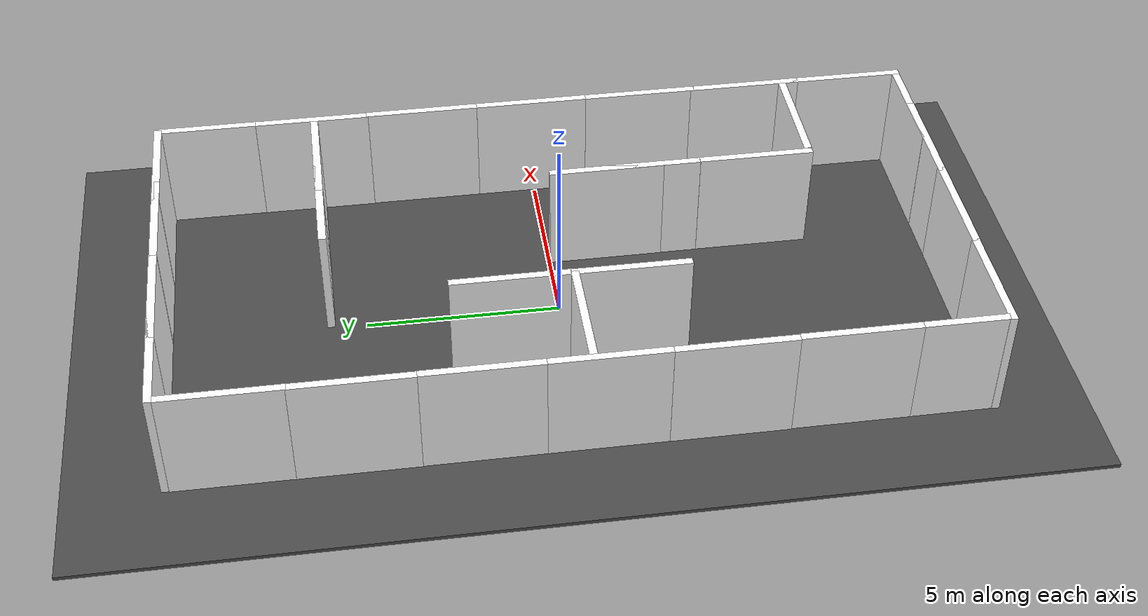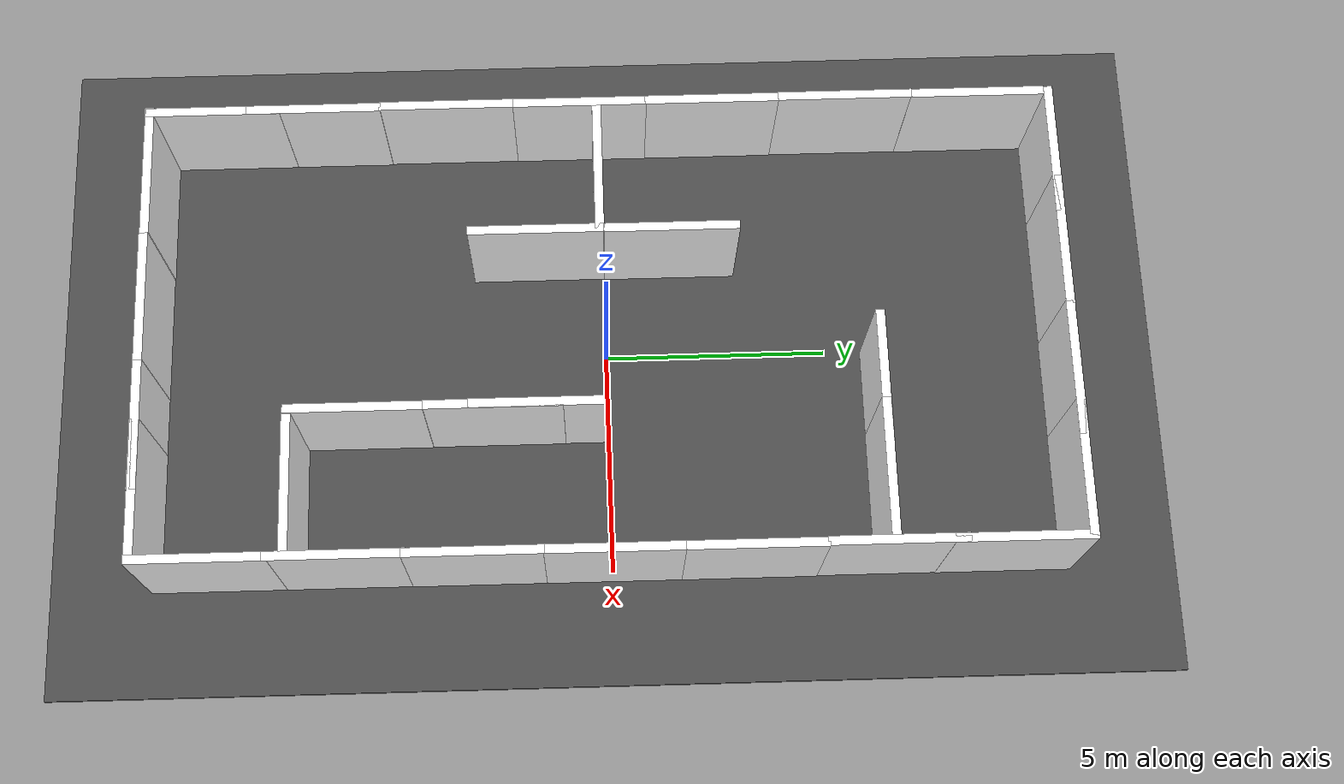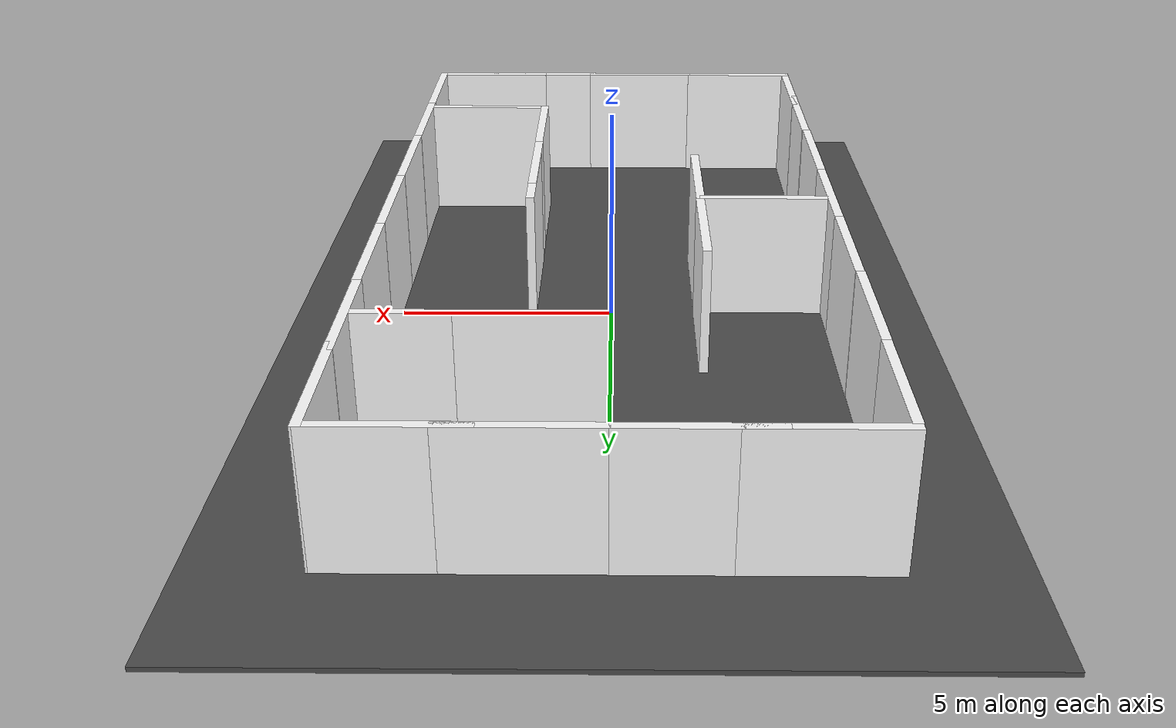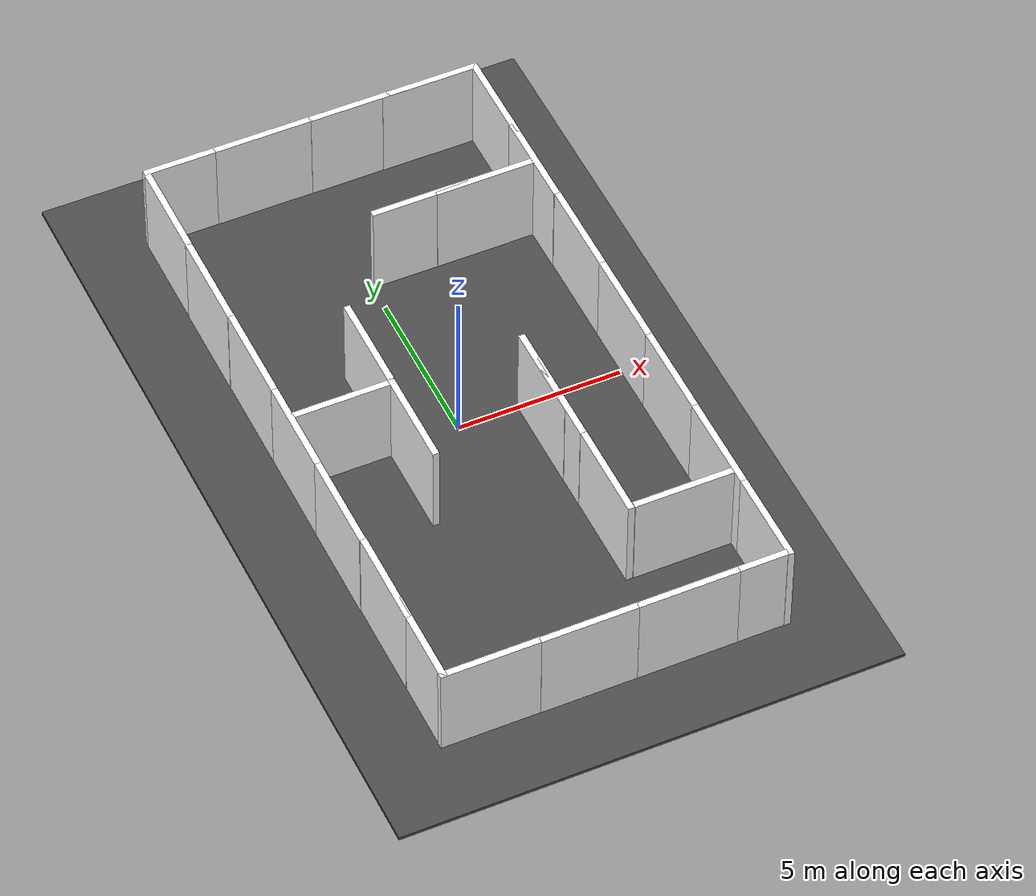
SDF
<sdf version="1.6">
 <world name="default">
  <light name="sun" type="directional">
   <pose>0 0 10 0 -0 0</pose>
   <diffuse>0.8 0.8 0.8 1</diffuse>
   <specular>0.2 0.2 0.2 1</specular>
   <attenuation>
    <range>1000</range>
    <constant>0.9</constant>
    <linear>0.01</linear>
    <quadratic>0.001</quadratic>
   </attenuation>
   <direction>-0.5 0.1 -0.9</direction>
  </light>
  <scene><ambient>0.4 0.4 0.4 1</ambient><background>0.7 0.7 0.7 1</background><shadows>1</shadows></scene>
  <spherical_coordinates>
   <surface_model>EARTH_WGS84</surface_model>
   <latitude_deg>0</latitude_deg>
   <longitude_deg>0</longitude_deg>
   <elevation>0</elevation>
   <heading_deg>0</heading_deg>
  </spherical_coordinates>
  <gravity>0 0 -9.8</gravity>
  <magnetic_field>6e-06 2.3e-05 -4.2e-05</magnetic_field>
  <atmosphere type="adiabatic"/>
  <audio><device>default</device></audio>
  <physics name="default_physics" default="0" type="ode">
   <max_step_size>0.001</max_step_size>
   <real_time_factor>1</real_time_factor>
   <real_time_update_rate>1000</real_time_update_rate>
  </physics>
  <model name="brick_box_3x0_2x3_0">
   <link name="chassis">
    <pose>0 0 1.5 0 -0 0</pose>
    <velocity_decay><linear>0</linear><angular>0</angular></velocity_decay>
    <inertial>
     <mass>1</mass>
     <inertia><ixx>1</ixx><ixy>0</ixy><ixz>0</ixz><iyy>1</iyy><iyz>0</iyz><izz>1</izz></inertia>
    </inertial>
    <visual name="visual">
     <geometry>
      <mesh><uri>model://brick_box_3x1x3/meshes/simple_box.dae</uri><scale>3 0.2 3</scale></mesh>
     </geometry>
     <material>
      <script>
       <uri>model://brick_box_3x1x3/materials/scripts</uri>
       <uri>model://brick_box_3x1x3/materials/textures</uri>
       <name>BrickBox/Diffuse</name>
      </script>
      <shader type="vertex"><normal_map>__default__</normal_map></shader>
      <ambient>1 1 1 1</ambient>
      <diffuse>1 1 1 1</diffuse>
      <specular>0 0 0 1</specular>
      <emissive>0 0 0 1</emissive>
     </material>
    </visual>
    <collision name="collision">
     <geometry><box><size>3 0.2 3</size></box></geometry>
     <surface>
      <friction>
       <ode><mu>1</mu><mu2>1</mu2><fdir1>0 0 0</fdir1><slip1>0</slip1><slip2>0</slip2></ode>
       <torsional>
        <coefficient>1</coefficient>
        <patch_radius>0</patch_radius>
        <surface_radius>0</surface_radius>
        <use_patch_radius>1</use_patch_radius>
        <ode><slip>0</slip></ode>
       </torsional>
      </friction>
      <bounce><restitution_coefficient>0</restitution_coefficient><threshold>1e+06</threshold></bounce>
      <contact>
       <collide_without_contact>0</collide_without_contact>
       <collide_without_contact_bitmask>1</collide_without_contact_bitmask>
       <collide_bitmask>1</collide_bitmask>
       <ode>
        <soft_cfm>0</soft_cfm>
        <soft_erp>0.2</soft_erp>
        <kp>1e+13</kp>
        <kd>1</kd>
        <max_vel>0.01</max_vel>
        <min_depth>0</min_depth>
       </ode>
       <bullet>
        <split_impulse>1</split_impulse>
        <split_impulse_penetration_threshold>-0.01</split_impulse_penetration_threshold>
        <soft_cfm>0</soft_cfm>
        <soft_erp>0.2</soft_erp>
        <kp>1e+13</kp>
        <kd>1</kd>
       </bullet>
      </contact>
     </surface>
    </collision>
   </link>
   <static>1</static>
   <pose>-1.51839 10.067 0 0 -0 0</pose>
  </model>
  <model name="brick_box_3x0_2x3_0_clone">
   <link name="chassis">
    <pose>0 0 1.5 0 -0 0</pose>
    <velocity_decay><linear>0</linear><angular>0</angular></velocity_decay>
    <inertial>
     <mass>1</mass>
     <inertia><ixx>1</ixx><ixy>0</ixy><ixz>0</ixz><iyy>1</iyy><iyz>0</iyz><izz>1</izz></inertia>
    </inertial>
    <visual name="visual">
     <geometry>
      <mesh><uri>model://brick_box_3x1x3/meshes/simple_box.dae</uri><scale>3 0.2 3</scale></mesh>
     </geometry>
     <material>
      <script>
       <uri>model://brick_box_3x1x3/materials/scripts</uri>
       <uri>model://brick_box_3x1x3/materials/textures</uri>
       <name>BrickBox/Diffuse</name>
      </script>
      <shader type="vertex"><normal_map>__default__</normal_map></shader>
      <ambient>1 1 1 1</ambient>
      <diffuse>1 1 1 1</diffuse>
      <specular>0 0 0 1</specular>
      <emissive>0 0 0 1</emissive>
     </material>
    </visual>
    <collision name="collision">
     <geometry><box><size>3 0.2 3</size></box></geometry>
     <surface>
      <friction>
       <ode><mu>1</mu><mu2>1</mu2><fdir1>0 0 0</fdir1><slip1>0</slip1><slip2>0</slip2></ode>
       <torsional>
        <coefficient>1</coefficient>
        <patch_radius>0</patch_radius>
        <surface_radius>0</surface_radius>
        <use_patch_radius>1</use_patch_radius>
        <ode><slip>0</slip></ode>
       </torsional>
      </friction>
      <bounce><restitution_coefficient>0</restitution_coefficient><threshold>1e+06</threshold></bounce>
      <contact>
       <collide_without_contact>0</collide_without_contact>
       <collide_without_contact_bitmask>1</collide_without_contact_bitmask>
       <collide_bitmask>1</collide_bitmask>
       <ode>
        <soft_cfm>0</soft_cfm>
        <soft_erp>0.2</soft_erp>
        <kp>1e+13</kp>
        <kd>1</kd>
        <max_vel>0.01</max_vel>
        <min_depth>0</min_depth>
       </ode>
       <bullet>
        <split_impulse>1</split_impulse>
        <split_impulse_penetration_threshold>-0.01</split_impulse_penetration_threshold>
        <soft_cfm>0</soft_cfm>
        <soft_erp>0.2</soft_erp>
        <kp>1e+13</kp>
        <kd>1</kd>
       </bullet>
      </contact>
     </surface>
    </collision>
   </link>
   <static>1</static>
   <pose>1.43593 10.0609 0 0 -0 0</pose>
  </model>
  <model name="brick_box_3x0_2x3_0_clone_0">
   <link name="chassis">
    <pose>0 0 1.5 0 -0 0</pose>
    <velocity_decay><linear>0</linear><angular>0</angular></velocity_decay>
    <inertial>
     <mass>1</mass>
     <inertia><ixx>1</ixx><ixy>0</ixy><ixz>0</ixz><iyy>1</iyy><iyz>0</iyz><izz>1</izz></inertia>
    </inertial>
    <visual name="visual">
     <geometry>
      <mesh><uri>model://brick_box_3x1x3/meshes/simple_box.dae</uri><scale>3 0.2 3</scale></mesh>
     </geometry>
     <material>
      <script>
       <uri>model://brick_box_3x1x3/materials/scripts</uri>
       <uri>model://brick_box_3x1x3/materials/textures</uri>
       <name>BrickBox/Diffuse</name>
      </script>
      <shader type="vertex"><normal_map>__default__</normal_map></shader>
      <ambient>1 1 1 1</ambient>
      <diffuse>1 1 1 1</diffuse>
      <specular>0 0 0 1</specular>
      <emissive>0 0 0 1</emissive>
     </material>
    </visual>
    <collision name="collision">
     <geometry><box><size>3 0.2 3</size></box></geometry>
     <surface>
      <friction>
       <ode><mu>1</mu><mu2>1</mu2><fdir1>0 0 0</fdir1><slip1>0</slip1><slip2>0</slip2></ode>
       <torsional>
        <coefficient>1</coefficient>
        <patch_radius>0</patch_radius>
        <surface_radius>0</surface_radius>
        <use_patch_radius>1</use_patch_radius>
        <ode><slip>0</slip></ode>
       </torsional>
      </friction>
      <bounce><restitution_coefficient>0</restitution_coefficient><threshold>1e+06</threshold></bounce>
      <contact>
       <collide_without_contact>0</collide_without_contact>
       <collide_without_contact_bitmask>1</collide_without_contact_bitmask>
       <collide_bitmask>1</collide_bitmask>
       <ode>
        <soft_cfm>0</soft_cfm>
        <soft_erp>0.2</soft_erp>
        <kp>1e+13</kp>
        <kd>1</kd>
        <max_vel>0.01</max_vel>
        <min_depth>0</min_depth>
       </ode>
       <bullet>
        <split_impulse>1</split_impulse>
        <split_impulse_penetration_threshold>-0.01</split_impulse_penetration_threshold>
        <soft_cfm>0</soft_cfm>
        <soft_erp>0.2</soft_erp>
        <kp>1e+13</kp>
        <kd>1</kd>
       </bullet>
      </contact>
     </surface>
    </collision>
   </link>
   <static>1</static>
   <pose>3.67716 10.056 0 0 -0 0</pose>
  </model>
  <model name="brick_box_3x0_2x3_0_clone_1">
   <link name="chassis">
    <pose>0 0 1.5 0 -0 0</pose>
    <velocity_decay><linear>0</linear><angular>0</angular></velocity_decay>
    <inertial>
     <mass>1</mass>
     <inertia><ixx>1</ixx><ixy>0</ixy><ixz>0</ixz><iyy>1</iyy><iyz>0</iyz><izz>1</izz></inertia>
    </inertial>
    <visual name="visual">
     <geometry>
      <mesh><uri>model://brick_box_3x1x3/meshes/simple_box.dae</uri><scale>3 0.2 3</scale></mesh>
     </geometry>
     <material>
      <script>
       <uri>model://brick_box_3x1x3/materials/scripts</uri>
       <uri>model://brick_box_3x1x3/materials/textures</uri>
       <name>BrickBox/Diffuse</name>
      </script>
      <shader type="vertex"><normal_map>__default__</normal_map></shader>
      <ambient>1 1 1 1</ambient>
      <diffuse>1 1 1 1</diffuse>
      <specular>0 0 0 1</specular>
      <emissive>0 0 0 1</emissive>
     </material>
    </visual>
    <collision name="collision">
     <geometry><box><size>3 0.2 3</size></box></geometry>
     <surface>
      <friction>
       <ode><mu>1</mu><mu2>1</mu2><fdir1>0 0 0</fdir1><slip1>0</slip1><slip2>0</slip2></ode>
       <torsional>
        <coefficient>1</coefficient>
        <patch_radius>0</patch_radius>
        <surface_radius>0</surface_radius>
        <use_patch_radius>1</use_patch_radius>
        <ode><slip>0</slip></ode>
       </torsional>
      </friction>
      <bounce><restitution_coefficient>0</restitution_coefficient><threshold>1e+06</threshold></bounce>
      <contact>
       <collide_without_contact>0</collide_without_contact>
       <collide_without_contact_bitmask>1</collide_without_contact_bitmask>
       <collide_bitmask>1</collide_bitmask>
       <ode>
        <soft_cfm>0</soft_cfm>
        <soft_erp>0.2</soft_erp>
        <kp>1e+13</kp>
        <kd>1</kd>
        <max_vel>0.01</max_vel>
        <min_depth>0</min_depth>
       </ode>
       <bullet>
        <split_impulse>1</split_impulse>
        <split_impulse_penetration_threshold>-0.01</split_impulse_penetration_threshold>
        <soft_cfm>0</soft_cfm>
        <soft_erp>0.2</soft_erp>
        <kp>1e+13</kp>
        <kd>1</kd>
       </bullet>
      </contact>
     </surface>
    </collision>
   </link>
   <static>1</static>
   <pose>-3.69017 10.0671 0 0 -0 0</pose>
  </model>
  <model name="brick_box_3x0_2x3_0_clone_2">
   <link name="chassis">
    <pose>0 0 1.5 0 -0 0</pose>
    <velocity_decay><linear>0</linear><angular>0</angular></velocity_decay>
    <inertial>
     <mass>1</mass>
     <inertia><ixx>1</ixx><ixy>0</ixy><ixz>0</ixz><iyy>1</iyy><iyz>0</iyz><izz>1</izz></inertia>
    </inertial>
    <visual name="visual">
     <geometry>
      <mesh><uri>model://brick_box_3x1x3/meshes/simple_box.dae</uri><scale>3 0.2 3</scale></mesh>
     </geometry>
     <material>
      <script>
       <uri>model://brick_box_3x1x3/materials/scripts</uri>
       <uri>model://brick_box_3x1x3/materials/textures</uri>
       <name>BrickBox/Diffuse</name>
      </script>
      <shader type="vertex"><normal_map>__default__</normal_map></shader>
      <ambient>1 1 1 1</ambient>
      <diffuse>1 1 1 1</diffuse>
      <specular>0 0 0 1</specular>
      <emissive>0 0 0 1</emissive>
     </material>
    </visual>
    <collision name="collision">
     <geometry><box><size>3 0.2 3</size></box></geometry>
     <surface>
      <friction>
       <ode><mu>1</mu><mu2>1</mu2><fdir1>0 0 0</fdir1><slip1>0</slip1><slip2>0</slip2></ode>
       <torsional>
        <coefficient>1</coefficient>
        <patch_radius>0</patch_radius>
        <surface_radius>0</surface_radius>
        <use_patch_radius>1</use_patch_radius>
        <ode><slip>0</slip></ode>
       </torsional>
      </friction>
      <bounce><restitution_coefficient>0</restitution_coefficient><threshold>1e+06</threshold></bounce>
      <contact>
       <collide_without_contact>0</collide_without_contact>
       <collide_without_contact_bitmask>1</collide_without_contact_bitmask>
       <collide_bitmask>1</collide_bitmask>
       <ode>
        <soft_cfm>0</soft_cfm>
        <soft_erp>0.2</soft_erp>
        <kp>1e+13</kp>
        <kd>1</kd>
        <max_vel>0.01</max_vel>
        <min_depth>0</min_depth>
       </ode>
       <bullet>
        <split_impulse>1</split_impulse>
        <split_impulse_penetration_threshold>-0.01</split_impulse_penetration_threshold>
        <soft_cfm>0</soft_cfm>
        <soft_erp>0.2</soft_erp>
        <kp>1e+13</kp>
        <kd>1</kd>
       </bullet>
      </contact>
     </surface>
    </collision>
   </link>
   <static>1</static>
   <pose>-5.10653 8.4779 0 0 -0 1.57</pose>
  </model>
  <model name="brick_box_3x0_2x3_0_clone_2_clone">
   <link name="chassis">
    <pose>0 0 1.5 0 -0 0</pose>
    <velocity_decay><linear>0</linear><angular>0</angular></velocity_decay>
    <inertial>
     <mass>1</mass>
     <inertia><ixx>1</ixx><ixy>0</ixy><ixz>0</ixz><iyy>1</iyy><iyz>0</iyz><izz>1</izz></inertia>
    </inertial>
    <visual name="visual">
     <geometry>
      <mesh><uri>model://brick_box_3x1x3/meshes/simple_box.dae</uri><scale>3 0.2 3</scale></mesh>
     </geometry>
     <material>
      <script>
       <uri>model://brick_box_3x1x3/materials/scripts</uri>
       <uri>model://brick_box_3x1x3/materials/textures</uri>
       <name>BrickBox/Diffuse</name>
      </script>
      <shader type="vertex"><normal_map>__default__</normal_map></shader>
      <ambient>1 1 1 1</ambient>
      <diffuse>1 1 1 1</diffuse>
      <specular>0 0 0 1</specular>
      <emissive>0 0 0 1</emissive>
     </material>
    </visual>
    <collision name="collision">
     <geometry><box><size>3 0.2 3</size></box></geometry>
     <surface>
      <friction>
       <ode><mu>1</mu><mu2>1</mu2><fdir1>0 0 0</fdir1><slip1>0</slip1><slip2>0</slip2></ode>
       <torsional>
        <coefficient>1</coefficient>
        <patch_radius>0</patch_radius>
        <surface_radius>0</surface_radius>
        <use_patch_radius>1</use_patch_radius>
        <ode><slip>0</slip></ode>
       </torsional>
      </friction>
      <bounce><restitution_coefficient>0</restitution_coefficient><threshold>1e+06</threshold></bounce>
      <contact>
       <collide_without_contact>0</collide_without_contact>
       <collide_without_contact_bitmask>1</collide_without_contact_bitmask>
       <collide_bitmask>1</collide_bitmask>
       <ode>
        <soft_cfm>0</soft_cfm>
        <soft_erp>0.2</soft_erp>
        <kp>1e+13</kp>
        <kd>1</kd>
        <max_vel>0.01</max_vel>
        <min_depth>0</min_depth>
       </ode>
       <bullet>
        <split_impulse>1</split_impulse>
        <split_impulse_penetration_threshold>-0.01</split_impulse_penetration_threshold>
        <soft_cfm>0</soft_cfm>
        <soft_erp>0.2</soft_erp>
        <kp>1e+13</kp>
        <kd>1</kd>
       </bullet>
      </contact>
     </surface>
    </collision>
   </link>
   <static>1</static>
   <pose>-5.11526 5.49974 0 0 -0 1.57</pose>
  </model>
  <model name="brick_box_3x0_2x3_0_clone_2_clone_0">
   <link name="chassis">
    <pose>0 0 1.5 0 -0 0</pose>
    <velocity_decay><linear>0</linear><angular>0</angular></velocity_decay>
    <inertial>
     <mass>1</mass>
     <inertia><ixx>1</ixx><ixy>0</ixy><ixz>0</ixz><iyy>1</iyy><iyz>0</iyz><izz>1</izz></inertia>
    </inertial>
    <visual name="visual">
     <geometry>
      <mesh><uri>model://brick_box_3x1x3/meshes/simple_box.dae</uri><scale>3 0.2 3</scale></mesh>
     </geometry>
     <material>
      <script>
       <uri>model://brick_box_3x1x3/materials/scripts</uri>
       <uri>model://brick_box_3x1x3/materials/textures</uri>
       <name>BrickBox/Diffuse</name>
      </script>
      <shader type="vertex"><normal_map>__default__</normal_map></shader>
      <ambient>1 1 1 1</ambient>
      <diffuse>1 1 1 1</diffuse>
      <specular>0 0 0 1</specular>
      <emissive>0 0 0 1</emissive>
     </material>
    </visual>
    <collision name="collision">
     <geometry><box><size>3 0.2 3</size></box></geometry>
     <surface>
      <friction>
       <ode><mu>1</mu><mu2>1</mu2><fdir1>0 0 0</fdir1><slip1>0</slip1><slip2>0</slip2></ode>
       <torsional>
        <coefficient>1</coefficient>
        <patch_radius>0</patch_radius>
        <surface_radius>0</surface_radius>
        <use_patch_radius>1</use_patch_radius>
        <ode><slip>0</slip></ode>
       </torsional>
      </friction>
      <bounce><restitution_coefficient>0</restitution_coefficient><threshold>1e+06</threshold></bounce>
      <contact>
       <collide_without_contact>0</collide_without_contact>
       <collide_without_contact_bitmask>1</collide_without_contact_bitmask>
       <collide_bitmask>1</collide_bitmask>
       <ode>
        <soft_cfm>0</soft_cfm>
        <soft_erp>0.2</soft_erp>
        <kp>1e+13</kp>
        <kd>1</kd>
        <max_vel>0.01</max_vel>
        <min_depth>0</min_depth>
       </ode>
       <bullet>
        <split_impulse>1</split_impulse>
        <split_impulse_penetration_threshold>-0.01</split_impulse_penetration_threshold>
        <soft_cfm>0</soft_cfm>
        <soft_erp>0.2</soft_erp>
        <kp>1e+13</kp>
        <kd>1</kd>
       </bullet>
      </contact>
     </surface>
    </collision>
   </link>
   <static>1</static>
   <pose>-5.10794 2.50232 0 0 -0 1.57</pose>
  </model>
  <model name="brick_box_3x0_2x3_0_clone_2_clone_1">
   <link name="chassis">
    <pose>0 0 1.5 0 -0 0</pose>
    <velocity_decay><linear>0</linear><angular>0</angular></velocity_decay>
    <inertial>
     <mass>1</mass>
     <inertia><ixx>1</ixx><ixy>0</ixy><ixz>0</ixz><iyy>1</iyy><iyz>0</iyz><izz>1</izz></inertia>
    </inertial>
    <visual name="visual">
     <geometry>
      <mesh><uri>model://brick_box_3x1x3/meshes/simple_box.dae</uri><scale>3 0.2 3</scale></mesh>
     </geometry>
     <material>
      <script>
       <uri>model://brick_box_3x1x3/materials/scripts</uri>
       <uri>model://brick_box_3x1x3/materials/textures</uri>
       <name>BrickBox/Diffuse</name>
      </script>
      <shader type="vertex"><normal_map>__default__</normal_map></shader>
      <ambient>1 1 1 1</ambient>
      <diffuse>1 1 1 1</diffuse>
      <specular>0 0 0 1</specular>
      <emissive>0 0 0 1</emissive>
     </material>
    </visual>
    <collision name="collision">
     <geometry><box><size>3 0.2 3</size></box></geometry>
     <surface>
      <friction>
       <ode><mu>1</mu><mu2>1</mu2><fdir1>0 0 0</fdir1><slip1>0</slip1><slip2>0</slip2></ode>
       <torsional>
        <coefficient>1</coefficient>
        <patch_radius>0</patch_radius>
        <surface_radius>0</surface_radius>
        <use_patch_radius>1</use_patch_radius>
        <ode><slip>0</slip></ode>
       </torsional>
      </friction>
      <bounce><restitution_coefficient>0</restitution_coefficient><threshold>1e+06</threshold></bounce>
      <contact>
       <collide_without_contact>0</collide_without_contact>
       <collide_without_contact_bitmask>1</collide_without_contact_bitmask>
       <collide_bitmask>1</collide_bitmask>
       <ode>
        <soft_cfm>0</soft_cfm>
        <soft_erp>0.2</soft_erp>
        <kp>1e+13</kp>
        <kd>1</kd>
        <max_vel>0.01</max_vel>
        <min_depth>0</min_depth>
       </ode>
       <bullet>
        <split_impulse>1</split_impulse>
        <split_impulse_penetration_threshold>-0.01</split_impulse_penetration_threshold>
        <soft_cfm>0</soft_cfm>
        <soft_erp>0.2</soft_erp>
        <kp>1e+13</kp>
        <kd>1</kd>
       </bullet>
      </contact>
     </surface>
    </collision>
   </link>
   <static>1</static>
   <pose>-5.10969 -0.466869 0 0 -0 1.57</pose>
  </model>
  <model name="brick_box_3x0_2x3_0_clone_2_clone_1_clone">
   <link name="chassis">
    <pose>0 0 1.5 0 -0 0</pose>
    <velocity_decay><linear>0</linear><angular>0</angular></velocity_decay>
    <inertial>
     <mass>1</mass>
     <inertia><ixx>1</ixx><ixy>0</ixy><ixz>0</ixz><iyy>1</iyy><iyz>0</iyz><izz>1</izz></inertia>
    </inertial>
    <visual name="visual">
     <geometry>
      <mesh><uri>model://brick_box_3x1x3/meshes/simple_box.dae</uri><scale>3 0.2 3</scale></mesh>
     </geometry>
     <material>
      <script>
       <uri>model://brick_box_3x1x3/materials/scripts</uri>
       <uri>model://brick_box_3x1x3/materials/textures</uri>
       <name>BrickBox/Diffuse</name>
      </script>
      <shader type="vertex"><normal_map>__default__</normal_map></shader>
      <ambient>1 1 1 1</ambient>
      <diffuse>1 1 1 1</diffuse>
      <specular>0 0 0 1</specular>
      <emissive>0 0 0 1</emissive>
     </material>
    </visual>
    <collision name="collision">
     <geometry><box><size>3 0.2 3</size></box></geometry>
     <surface>
      <friction>
       <ode><mu>1</mu><mu2>1</mu2><fdir1>0 0 0</fdir1><slip1>0</slip1><slip2>0</slip2></ode>
       <torsional>
        <coefficient>1</coefficient>
        <patch_radius>0</patch_radius>
        <surface_radius>0</surface_radius>
        <use_patch_radius>1</use_patch_radius>
        <ode><slip>0</slip></ode>
       </torsional>
      </friction>
      <bounce><restitution_coefficient>0</restitution_coefficient><threshold>1e+06</threshold></bounce>
      <contact>
       <collide_without_contact>0</collide_without_contact>
       <collide_without_contact_bitmask>1</collide_without_contact_bitmask>
       <collide_bitmask>1</collide_bitmask>
       <ode>
        <soft_cfm>0</soft_cfm>
        <soft_erp>0.2</soft_erp>
        <kp>1e+13</kp>
        <kd>1</kd>
        <max_vel>0.01</max_vel>
        <min_depth>0</min_depth>
       </ode>
       <bullet>
        <split_impulse>1</split_impulse>
        <split_impulse_penetration_threshold>-0.01</split_impulse_penetration_threshold>
        <soft_cfm>0</soft_cfm>
        <soft_erp>0.2</soft_erp>
        <kp>1e+13</kp>
        <kd>1</kd>
       </bullet>
      </contact>
     </surface>
    </collision>
   </link>
   <static>1</static>
   <pose>-5.11767 -3.46485 0 0 -0 1.57</pose>
  </model>
  <model name="brick_box_3x0_2x3_0_clone_2_clone_1_clone_0">
   <link name="chassis">
    <pose>0 0 1.5 0 -0 0</pose>
    <velocity_decay><linear>0</linear><angular>0</angular></velocity_decay>
    <inertial>
     <mass>1</mass>
     <inertia><ixx>1</ixx><ixy>0</ixy><ixz>0</ixz><iyy>1</iyy><iyz>0</iyz><izz>1</izz></inertia>
    </inertial>
    <visual name="visual">
     <geometry>
      <mesh><uri>model://brick_box_3x1x3/meshes/simple_box.dae</uri><scale>3 0.2 3</scale></mesh>
     </geometry>
     <material>
      <script>
       <uri>model://brick_box_3x1x3/materials/scripts</uri>
       <uri>model://brick_box_3x1x3/materials/textures</uri>
       <name>BrickBox/Diffuse</name>
      </script>
      <shader type="vertex"><normal_map>__default__</normal_map></shader>
      <ambient>1 1 1 1</ambient>
      <diffuse>1 1 1 1</diffuse>
      <specular>0 0 0 1</specular>
      <emissive>0 0 0 1</emissive>
     </material>
    </visual>
    <collision name="collision">
     <geometry><box><size>3 0.2 3</size></box></geometry>
     <surface>
      <friction>
       <ode><mu>1</mu><mu2>1</mu2><fdir1>0 0 0</fdir1><slip1>0</slip1><slip2>0</slip2></ode>
       <torsional>
        <coefficient>1</coefficient>
        <patch_radius>0</patch_radius>
        <surface_radius>0</surface_radius>
        <use_patch_radius>1</use_patch_radius>
        <ode><slip>0</slip></ode>
       </torsional>
      </friction>
      <bounce><restitution_coefficient>0</restitution_coefficient><threshold>1e+06</threshold></bounce>
      <contact>
       <collide_without_contact>0</collide_without_contact>
       <collide_without_contact_bitmask>1</collide_without_contact_bitmask>
       <collide_bitmask>1</collide_bitmask>
       <ode>
        <soft_cfm>0</soft_cfm>
        <soft_erp>0.2</soft_erp>
        <kp>1e+13</kp>
        <kd>1</kd>
        <max_vel>0.01</max_vel>
        <min_depth>0</min_depth>
       </ode>
       <bullet>
        <split_impulse>1</split_impulse>
        <split_impulse_penetration_threshold>-0.01</split_impulse_penetration_threshold>
        <soft_cfm>0</soft_cfm>
        <soft_erp>0.2</soft_erp>
        <kp>1e+13</kp>
        <kd>1</kd>
       </bullet>
      </contact>
     </surface>
    </collision>
   </link>
   <static>1</static>
   <pose>-5.10293 -6.4385 0 0 -0 1.57</pose>
  </model>
  <model name="brick_box_3x0_2x3_0_clone_2_clone_1_clone_1">
   <link name="chassis">
    <pose>0 0 1.5 0 -0 0</pose>
    <velocity_decay><linear>0</linear><angular>0</angular></velocity_decay>
    <inertial>
     <mass>1</mass>
     <inertia><ixx>1</ixx><ixy>0</ixy><ixz>0</ixz><iyy>1</iyy><iyz>0</iyz><izz>1</izz></inertia>
    </inertial>
    <visual name="visual">
     <geometry>
      <mesh><uri>model://brick_box_3x1x3/meshes/simple_box.dae</uri><scale>3 0.2 3</scale></mesh>
     </geometry>
     <material>
      <script>
       <uri>model://brick_box_3x1x3/materials/scripts</uri>
       <uri>model://brick_box_3x1x3/materials/textures</uri>
       <name>BrickBox/Diffuse</name>
      </script>
      <shader type="vertex"><normal_map>__default__</normal_map></shader>
      <ambient>1 1 1 1</ambient>
      <diffuse>1 1 1 1</diffuse>
      <specular>0 0 0 1</specular>
      <emissive>0 0 0 1</emissive>
     </material>
    </visual>
    <collision name="collision">
     <geometry><box><size>3 0.2 3</size></box></geometry>
     <surface>
      <friction>
       <ode><mu>1</mu><mu2>1</mu2><fdir1>0 0 0</fdir1><slip1>0</slip1><slip2>0</slip2></ode>
       <torsional>
        <coefficient>1</coefficient>
        <patch_radius>0</patch_radius>
        <surface_radius>0</surface_radius>
        <use_patch_radius>1</use_patch_radius>
        <ode><slip>0</slip></ode>
       </torsional>
      </friction>
      <bounce><restitution_coefficient>0</restitution_coefficient><threshold>1e+06</threshold></bounce>
      <contact>
       <collide_without_contact>0</collide_without_contact>
       <collide_without_contact_bitmask>1</collide_without_contact_bitmask>
       <collide_bitmask>1</collide_bitmask>
       <ode>
        <soft_cfm>0</soft_cfm>
        <soft_erp>0.2</soft_erp>
        <kp>1e+13</kp>
        <kd>1</kd>
        <max_vel>0.01</max_vel>
        <min_depth>0</min_depth>
       </ode>
       <bullet>
        <split_impulse>1</split_impulse>
        <split_impulse_penetration_threshold>-0.01</split_impulse_penetration_threshold>
        <soft_cfm>0</soft_cfm>
        <soft_erp>0.2</soft_erp>
        <kp>1e+13</kp>
        <kd>1</kd>
       </bullet>
      </contact>
     </surface>
    </collision>
   </link>
   <static>1</static>
   <pose>-5.10132 -8.68929 0 0 -0 1.57</pose>
  </model>
  <model name="brick_box_3x0_2x3_0_clone_1_clone">
   <link name="chassis">
    <pose>0 0 1.5 0 -0 0</pose>
    <velocity_decay><linear>0</linear><angular>0</angular></velocity_decay>
    <inertial>
     <mass>1</mass>
     <inertia><ixx>1</ixx><ixy>0</ixy><ixz>0</ixz><iyy>1</iyy><iyz>0</iyz><izz>1</izz></inertia>
    </inertial>
    <visual name="visual">
     <geometry>
      <mesh><uri>model://brick_box_3x1x3/meshes/simple_box.dae</uri><scale>3 0.2 3</scale></mesh>
     </geometry>
     <material>
      <script>
       <uri>model://brick_box_3x1x3/materials/scripts</uri>
       <uri>model://brick_box_3x1x3/materials/textures</uri>
       <name>BrickBox/Diffuse</name>
      </script>
      <shader type="vertex"><normal_map>__default__</normal_map></shader>
      <ambient>1 1 1 1</ambient>
      <diffuse>1 1 1 1</diffuse>
      <specular>0 0 0 1</specular>
      <emissive>0 0 0 1</emissive>
     </material>
    </visual>
    <collision name="collision">
     <geometry><box><size>3 0.2 3</size></box></geometry>
     <surface>
      <friction>
       <ode><mu>1</mu><mu2>1</mu2><fdir1>0 0 0</fdir1><slip1>0</slip1><slip2>0</slip2></ode>
       <torsional>
        <coefficient>1</coefficient>
        <patch_radius>0</patch_radius>
        <surface_radius>0</surface_radius>
        <use_patch_radius>1</use_patch_radius>
        <ode><slip>0</slip></ode>
       </torsional>
      </friction>
      <bounce><restitution_coefficient>0</restitution_coefficient><threshold>1e+06</threshold></bounce>
      <contact>
       <collide_without_contact>0</collide_without_contact>
       <collide_without_contact_bitmask>1</collide_without_contact_bitmask>
       <collide_bitmask>1</collide_bitmask>
       <ode>
        <soft_cfm>0</soft_cfm>
        <soft_erp>0.2</soft_erp>
        <kp>1e+13</kp>
        <kd>1</kd>
        <max_vel>0.01</max_vel>
        <min_depth>0</min_depth>
       </ode>
       <bullet>
        <split_impulse>1</split_impulse>
        <split_impulse_penetration_threshold>-0.01</split_impulse_penetration_threshold>
        <soft_cfm>0</soft_cfm>
        <soft_erp>0.2</soft_erp>
        <kp>1e+13</kp>
        <kd>1</kd>
       </bullet>
      </contact>
     </surface>
    </collision>
   </link>
   <static>1</static>
   <pose>-3.71023 -10.0958 0 0 -0 0</pose>
  </model>
  <model name="brick_box_3x0_2x3_0_clone_1_clone_clone">
   <link name="chassis">
    <pose>0 0 1.5 0 -0 0</pose>
    <velocity_decay><linear>0</linear><angular>0</angular></velocity_decay>
    <inertial>
     <mass>1</mass>
     <inertia><ixx>1</ixx><ixy>0</ixy><ixz>0</ixz><iyy>1</iyy><iyz>0</iyz><izz>1</izz></inertia>
    </inertial>
    <visual name="visual">
     <geometry>
      <mesh><uri>model://brick_box_3x1x3/meshes/simple_box.dae</uri><scale>3 0.2 3</scale></mesh>
     </geometry>
     <material>
      <script>
       <uri>model://brick_box_3x1x3/materials/scripts</uri>
       <uri>model://brick_box_3x1x3/materials/textures</uri>
       <name>BrickBox/Diffuse</name>
      </script>
      <shader type="vertex"><normal_map>__default__</normal_map></shader>
      <ambient>1 1 1 1</ambient>
      <diffuse>1 1 1 1</diffuse>
      <specular>0 0 0 1</specular>
      <emissive>0 0 0 1</emissive>
     </material>
    </visual>
    <collision name="collision">
     <geometry><box><size>3 0.2 3</size></box></geometry>
     <surface>
      <friction>
       <ode><mu>1</mu><mu2>1</mu2><fdir1>0 0 0</fdir1><slip1>0</slip1><slip2>0</slip2></ode>
       <torsional>
        <coefficient>1</coefficient>
        <patch_radius>0</patch_radius>
        <surface_radius>0</surface_radius>
        <use_patch_radius>1</use_patch_radius>
        <ode><slip>0</slip></ode>
       </torsional>
      </friction>
      <bounce><restitution_coefficient>0</restitution_coefficient><threshold>1e+06</threshold></bounce>
      <contact>
       <collide_without_contact>0</collide_without_contact>
       <collide_without_contact_bitmask>1</collide_without_contact_bitmask>
       <collide_bitmask>1</collide_bitmask>
       <ode>
        <soft_cfm>0</soft_cfm>
        <soft_erp>0.2</soft_erp>
        <kp>1e+13</kp>
        <kd>1</kd>
        <max_vel>0.01</max_vel>
        <min_depth>0</min_depth>
       </ode>
       <bullet>
        <split_impulse>1</split_impulse>
        <split_impulse_penetration_threshold>-0.01</split_impulse_penetration_threshold>
        <soft_cfm>0</soft_cfm>
        <soft_erp>0.2</soft_erp>
        <kp>1e+13</kp>
        <kd>1</kd>
       </bullet>
      </contact>
     </surface>
    </collision>
   </link>
   <static>1</static>
   <pose>-0.774829 -10.1072 0 0 -0 0</pose>
  </model>
  <model name="brick_box_3x0_2x3_0_clone_1_clone_clone_0">
   <link name="chassis">
    <pose>0 0 1.5 0 -0 0</pose>
    <velocity_decay><linear>0</linear><angular>0</angular></velocity_decay>
    <inertial>
     <mass>1</mass>
     <inertia><ixx>1</ixx><ixy>0</ixy><ixz>0</ixz><iyy>1</iyy><iyz>0</iyz><izz>1</izz></inertia>
    </inertial>
    <visual name="visual">
     <geometry>
      <mesh><uri>model://brick_box_3x1x3/meshes/simple_box.dae</uri><scale>3 0.2 3</scale></mesh>
     </geometry>
     <material>
      <script>
       <uri>model://brick_box_3x1x3/materials/scripts</uri>
       <uri>model://brick_box_3x1x3/materials/textures</uri>
       <name>BrickBox/Diffuse</name>
      </script>
      <shader type="vertex"><normal_map>__default__</normal_map></shader>
      <ambient>1 1 1 1</ambient>
      <diffuse>1 1 1 1</diffuse>
      <specular>0 0 0 1</specular>
      <emissive>0 0 0 1</emissive>
     </material>
    </visual>
    <collision name="collision">
     <geometry><box><size>3 0.2 3</size></box></geometry>
     <surface>
      <friction>
       <ode><mu>1</mu><mu2>1</mu2><fdir1>0 0 0</fdir1><slip1>0</slip1><slip2>0</slip2></ode>
       <torsional>
        <coefficient>1</coefficient>
        <patch_radius>0</patch_radius>
        <surface_radius>0</surface_radius>
        <use_patch_radius>1</use_patch_radius>
        <ode><slip>0</slip></ode>
       </torsional>
      </friction>
      <bounce><restitution_coefficient>0</restitution_coefficient><threshold>1e+06</threshold></bounce>
      <contact>
       <collide_without_contact>0</collide_without_contact>
       <collide_without_contact_bitmask>1</collide_without_contact_bitmask>
       <collide_bitmask>1</collide_bitmask>
       <ode>
        <soft_cfm>0</soft_cfm>
        <soft_erp>0.2</soft_erp>
        <kp>1e+13</kp>
        <kd>1</kd>
        <max_vel>0.01</max_vel>
        <min_depth>0</min_depth>
       </ode>
       <bullet>
        <split_impulse>1</split_impulse>
        <split_impulse_penetration_threshold>-0.01</split_impulse_penetration_threshold>
        <soft_cfm>0</soft_cfm>
        <soft_erp>0.2</soft_erp>
        <kp>1e+13</kp>
        <kd>1</kd>
       </bullet>
      </contact>
     </surface>
    </collision>
   </link>
   <static>1</static>
   <pose>2.09652 -10.1097 0 0 -0 0</pose>
  </model>
  <model name="brick_box_3x0_2x3_0_clone_1_clone_clone_1">
   <link name="chassis">
    <pose>0 0 1.5 0 -0 0</pose>
    <velocity_decay><linear>0</linear><angular>0</angular></velocity_decay>
    <inertial>
     <mass>1</mass>
     <inertia><ixx>1</ixx><ixy>0</ixy><ixz>0</ixz><iyy>1</iyy><iyz>0</iyz><izz>1</izz></inertia>
    </inertial>
    <visual name="visual">
     <geometry>
      <mesh><uri>model://brick_box_3x1x3/meshes/simple_box.dae</uri><scale>3 0.2 3</scale></mesh>
     </geometry>
     <material>
      <script>
       <uri>model://brick_box_3x1x3/materials/scripts</uri>
       <uri>model://brick_box_3x1x3/materials/textures</uri>
       <name>BrickBox/Diffuse</name>
      </script>
      <shader type="vertex"><normal_map>__default__</normal_map></shader>
      <ambient>1 1 1 1</ambient>
      <diffuse>1 1 1 1</diffuse>
      <specular>0 0 0 1</specular>
      <emissive>0 0 0 1</emissive>
     </material>
    </visual>
    <collision name="collision">
     <geometry><box><size>3 0.2 3</size></box></geometry>
     <surface>
      <friction>
       <ode><mu>1</mu><mu2>1</mu2><fdir1>0 0 0</fdir1><slip1>0</slip1><slip2>0</slip2></ode>
       <torsional>
        <coefficient>1</coefficient>
        <patch_radius>0</patch_radius>
        <surface_radius>0</surface_radius>
        <use_patch_radius>1</use_patch_radius>
        <ode><slip>0</slip></ode>
       </torsional>
      </friction>
      <bounce><restitution_coefficient>0</restitution_coefficient><threshold>1e+06</threshold></bounce>
      <contact>
       <collide_without_contact>0</collide_without_contact>
       <collide_without_contact_bitmask>1</collide_without_contact_bitmask>
       <collide_bitmask>1</collide_bitmask>
       <ode>
        <soft_cfm>0</soft_cfm>
        <soft_erp>0.2</soft_erp>
        <kp>1e+13</kp>
        <kd>1</kd>
        <max_vel>0.01</max_vel>
        <min_depth>0</min_depth>
       </ode>
       <bullet>
        <split_impulse>1</split_impulse>
        <split_impulse_penetration_threshold>-0.01</split_impulse_penetration_threshold>
        <soft_cfm>0</soft_cfm>
        <soft_erp>0.2</soft_erp>
        <kp>1e+13</kp>
        <kd>1</kd>
       </bullet>
      </contact>
     </surface>
    </collision>
   </link>
   <static>1</static>
   <pose>3.54888 -10.1055 0 0 -0 0</pose>
  </model>
  <model name="brick_box_3x0_2x3_0_clone_2_clone_1_clone_1_clone">
   <link name="chassis">
    <pose>0 0 1.5 0 -0 0</pose>
    <velocity_decay><linear>0</linear><angular>0</angular></velocity_decay>
    <inertial>
     <mass>1</mass>
     <inertia><ixx>1</ixx><ixy>0</ixy><ixz>0</ixz><iyy>1</iyy><iyz>0</iyz><izz>1</izz></inertia>
    </inertial>
    <visual name="visual">
     <geometry>
      <mesh><uri>model://brick_box_3x1x3/meshes/simple_box.dae</uri><scale>3 0.2 3</scale></mesh>
     </geometry>
     <material>
      <script>
       <uri>model://brick_box_3x1x3/materials/scripts</uri>
       <uri>model://brick_box_3x1x3/materials/textures</uri>
       <name>BrickBox/Diffuse</name>
      </script>
      <shader type="vertex"><normal_map>__default__</normal_map></shader>
      <ambient>1 1 1 1</ambient>
      <diffuse>1 1 1 1</diffuse>
      <specular>0 0 0 1</specular>
      <emissive>0 0 0 1</emissive>
     </material>
    </visual>
    <collision name="collision">
     <geometry><box><size>3 0.2 3</size></box></geometry>
     <surface>
      <friction>
       <ode><mu>1</mu><mu2>1</mu2><fdir1>0 0 0</fdir1><slip1>0</slip1><slip2>0</slip2></ode>
       <torsional>
        <coefficient>1</coefficient>
        <patch_radius>0</patch_radius>
        <surface_radius>0</surface_radius>
        <use_patch_radius>1</use_patch_radius>
        <ode><slip>0</slip></ode>
       </torsional>
      </friction>
      <bounce><restitution_coefficient>0</restitution_coefficient><threshold>1e+06</threshold></bounce>
      <contact>
       <collide_without_contact>0</collide_without_contact>
       <collide_without_contact_bitmask>1</collide_without_contact_bitmask>
       <collide_bitmask>1</collide_bitmask>
       <ode>
        <soft_cfm>0</soft_cfm>
        <soft_erp>0.2</soft_erp>
        <kp>1e+13</kp>
        <kd>1</kd>
        <max_vel>0.01</max_vel>
        <min_depth>0</min_depth>
       </ode>
       <bullet>
        <split_impulse>1</split_impulse>
        <split_impulse_penetration_threshold>-0.01</split_impulse_penetration_threshold>
        <soft_cfm>0</soft_cfm>
        <soft_erp>0.2</soft_erp>
        <kp>1e+13</kp>
        <kd>1</kd>
       </bullet>
      </contact>
     </surface>
    </collision>
   </link>
   <static>1</static>
   <pose>5.10532 -8.71765 0 0 -0 1.57</pose>
  </model>
  <model name="brick_box_3x0_2x3_0_clone_2_clone_1_clone_1_clone_0">
   <link name="chassis">
    <pose>0 0 1.5 0 -0 0</pose>
    <velocity_decay><linear>0</linear><angular>0</angular></velocity_decay>
    <inertial>
     <mass>1</mass>
     <inertia><ixx>1</ixx><ixy>0</ixy><ixz>0</ixz><iyy>1</iyy><iyz>0</iyz><izz>1</izz></inertia>
    </inertial>
    <visual name="visual">
     <geometry>
      <mesh><uri>model://brick_box_3x1x3/meshes/simple_box.dae</uri><scale>3 0.2 3</scale></mesh>
     </geometry>
     <material>
      <script>
       <uri>model://brick_box_3x1x3/materials/scripts</uri>
       <uri>model://brick_box_3x1x3/materials/textures</uri>
       <name>BrickBox/Diffuse</name>
      </script>
      <shader type="vertex"><normal_map>__default__</normal_map></shader>
      <ambient>1 1 1 1</ambient>
      <diffuse>1 1 1 1</diffuse>
      <specular>0 0 0 1</specular>
      <emissive>0 0 0 1</emissive>
     </material>
    </visual>
    <collision name="collision">
     <geometry><box><size>3 0.2 3</size></box></geometry>
     <surface>
      <friction>
       <ode><mu>1</mu><mu2>1</mu2><fdir1>0 0 0</fdir1><slip1>0</slip1><slip2>0</slip2></ode>
       <torsional>
        <coefficient>1</coefficient>
        <patch_radius>0</patch_radius>
        <surface_radius>0</surface_radius>
        <use_patch_radius>1</use_patch_radius>
        <ode><slip>0</slip></ode>
       </torsional>
      </friction>
      <bounce><restitution_coefficient>0</restitution_coefficient><threshold>1e+06</threshold></bounce>
      <contact>
       <collide_without_contact>0</collide_without_contact>
       <collide_without_contact_bitmask>1</collide_without_contact_bitmask>
       <collide_bitmask>1</collide_bitmask>
       <ode>
        <soft_cfm>0</soft_cfm>
        <soft_erp>0.2</soft_erp>
        <kp>1e+13</kp>
        <kd>1</kd>
        <max_vel>0.01</max_vel>
        <min_depth>0</min_depth>
       </ode>
       <bullet>
        <split_impulse>1</split_impulse>
        <split_impulse_penetration_threshold>-0.01</split_impulse_penetration_threshold>
        <soft_cfm>0</soft_cfm>
        <soft_erp>0.2</soft_erp>
        <kp>1e+13</kp>
        <kd>1</kd>
       </bullet>
      </contact>
     </surface>
    </collision>
   </link>
   <static>1</static>
   <pose>5.10701 -5.83783 0 0 -0 1.57</pose>
  </model>
  <model name="brick_box_3x0_2x3_0_clone_2_clone_1_clone_1_clone_1">
   <link name="chassis">
    <pose>0 0 1.5 0 -0 0</pose>
    <velocity_decay><linear>0</linear><angular>0</angular></velocity_decay>
    <inertial>
     <mass>1</mass>
     <inertia><ixx>1</ixx><ixy>0</ixy><ixz>0</ixz><iyy>1</iyy><iyz>0</iyz><izz>1</izz></inertia>
    </inertial>
    <visual name="visual">
     <geometry>
      <mesh><uri>model://brick_box_3x1x3/meshes/simple_box.dae</uri><scale>3 0.2 3</scale></mesh>
     </geometry>
     <material>
      <script>
       <uri>model://brick_box_3x1x3/materials/scripts</uri>
       <uri>model://brick_box_3x1x3/materials/textures</uri>
       <name>BrickBox/Diffuse</name>
      </script>
      <shader type="vertex"><normal_map>__default__</normal_map></shader>
      <ambient>1 1 1 1</ambient>
      <diffuse>1 1 1 1</diffuse>
      <specular>0 0 0 1</specular>
      <emissive>0 0 0 1</emissive>
     </material>
    </visual>
    <collision name="collision">
     <geometry><box><size>3 0.2 3</size></box></geometry>
     <surface>
      <friction>
       <ode><mu>1</mu><mu2>1</mu2><fdir1>0 0 0</fdir1><slip1>0</slip1><slip2>0</slip2></ode>
       <torsional>
        <coefficient>1</coefficient>
        <patch_radius>0</patch_radius>
        <surface_radius>0</surface_radius>
        <use_patch_radius>1</use_patch_radius>
        <ode><slip>0</slip></ode>
       </torsional>
      </friction>
      <bounce><restitution_coefficient>0</restitution_coefficient><threshold>1e+06</threshold></bounce>
      <contact>
       <collide_without_contact>0</collide_without_contact>
       <collide_without_contact_bitmask>1</collide_without_contact_bitmask>
       <collide_bitmask>1</collide_bitmask>
       <ode>
        <soft_cfm>0</soft_cfm>
        <soft_erp>0.2</soft_erp>
        <kp>1e+13</kp>
        <kd>1</kd>
        <max_vel>0.01</max_vel>
        <min_depth>0</min_depth>
       </ode>
       <bullet>
        <split_impulse>1</split_impulse>
        <split_impulse_penetration_threshold>-0.01</split_impulse_penetration_threshold>
        <soft_cfm>0</soft_cfm>
        <soft_erp>0.2</soft_erp>
        <kp>1e+13</kp>
        <kd>1</kd>
       </bullet>
      </contact>
     </surface>
    </collision>
   </link>
   <static>1</static>
   <pose>5.11388 -2.93601 0 0 -0 1.57</pose>
  </model>
  <model name="brick_box_3x0_2x3_0_clone_2_clone_1_clone_1_clone_2">
   <link name="chassis">
    <pose>0 0 1.5 0 -0 0</pose>
    <velocity_decay><linear>0</linear><angular>0</angular></velocity_decay>
    <inertial>
     <mass>1</mass>
     <inertia><ixx>1</ixx><ixy>0</ixy><ixz>0</ixz><iyy>1</iyy><iyz>0</iyz><izz>1</izz></inertia>
    </inertial>
    <visual name="visual">
     <geometry>
      <mesh><uri>model://brick_box_3x1x3/meshes/simple_box.dae</uri><scale>3 0.2 3</scale></mesh>
     </geometry>
     <material>
      <script>
       <uri>model://brick_box_3x1x3/materials/scripts</uri>
       <uri>model://brick_box_3x1x3/materials/textures</uri>
       <name>BrickBox/Diffuse</name>
      </script>
      <shader type="vertex"><normal_map>__default__</normal_map></shader>
      <ambient>1 1 1 1</ambient>
      <diffuse>1 1 1 1</diffuse>
      <specular>0 0 0 1</specular>
      <emissive>0 0 0 1</emissive>
     </material>
    </visual>
    <collision name="collision">
     <geometry><box><size>3 0.2 3</size></box></geometry>
     <surface>
      <friction>
       <ode><mu>1</mu><mu2>1</mu2><fdir1>0 0 0</fdir1><slip1>0</slip1><slip2>0</slip2></ode>
       <torsional>
        <coefficient>1</coefficient>
        <patch_radius>0</patch_radius>
        <surface_radius>0</surface_radius>
        <use_patch_radius>1</use_patch_radius>
        <ode><slip>0</slip></ode>
       </torsional>
      </friction>
      <bounce><restitution_coefficient>0</restitution_coefficient><threshold>1e+06</threshold></bounce>
      <contact>
       <collide_without_contact>0</collide_without_contact>
       <collide_without_contact_bitmask>1</collide_without_contact_bitmask>
       <collide_bitmask>1</collide_bitmask>
       <ode>
        <soft_cfm>0</soft_cfm>
        <soft_erp>0.2</soft_erp>
        <kp>1e+13</kp>
        <kd>1</kd>
        <max_vel>0.01</max_vel>
        <min_depth>0</min_depth>
       </ode>
       <bullet>
        <split_impulse>1</split_impulse>
        <split_impulse_penetration_threshold>-0.01</split_impulse_penetration_threshold>
        <soft_cfm>0</soft_cfm>
        <soft_erp>0.2</soft_erp>
        <kp>1e+13</kp>
        <kd>1</kd>
       </bullet>
      </contact>
     </surface>
    </collision>
   </link>
   <static>1</static>
   <pose>5.11899 0.040939 0 0 -0 1.57</pose>
  </model>
  <model name="brick_box_3x0_2x3_0_clone_2_clone_1_clone_1_clone_3">
   <link name="chassis">
    <pose>0 0 1.5 0 -0 0</pose>
    <velocity_decay><linear>0</linear><angular>0</angular></velocity_decay>
    <inertial>
     <mass>1</mass>
     <inertia><ixx>1</ixx><ixy>0</ixy><ixz>0</ixz><iyy>1</iyy><iyz>0</iyz><izz>1</izz></inertia>
    </inertial>
    <visual name="visual">
     <geometry>
      <mesh><uri>model://brick_box_3x1x3/meshes/simple_box.dae</uri><scale>3 0.2 3</scale></mesh>
     </geometry>
     <material>
      <script>
       <uri>model://brick_box_3x1x3/materials/scripts</uri>
       <uri>model://brick_box_3x1x3/materials/textures</uri>
       <name>BrickBox/Diffuse</name>
      </script>
      <shader type="vertex"><normal_map>__default__</normal_map></shader>
      <ambient>1 1 1 1</ambient>
      <diffuse>1 1 1 1</diffuse>
      <specular>0 0 0 1</specular>
      <emissive>0 0 0 1</emissive>
     </material>
    </visual>
    <collision name="collision">
     <geometry><box><size>3 0.2 3</size></box></geometry>
     <surface>
      <friction>
       <ode><mu>1</mu><mu2>1</mu2><fdir1>0 0 0</fdir1><slip1>0</slip1><slip2>0</slip2></ode>
       <torsional>
        <coefficient>1</coefficient>
        <patch_radius>0</patch_radius>
        <surface_radius>0</surface_radius>
        <use_patch_radius>1</use_patch_radius>
        <ode><slip>0</slip></ode>
       </torsional>
      </friction>
      <bounce><restitution_coefficient>0</restitution_coefficient><threshold>1e+06</threshold></bounce>
      <contact>
       <collide_without_contact>0</collide_without_contact>
       <collide_without_contact_bitmask>1</collide_without_contact_bitmask>
       <collide_bitmask>1</collide_bitmask>
       <ode>
        <soft_cfm>0</soft_cfm>
        <soft_erp>0.2</soft_erp>
        <kp>1e+13</kp>
        <kd>1</kd>
        <max_vel>0.01</max_vel>
        <min_depth>0</min_depth>
       </ode>
       <bullet>
        <split_impulse>1</split_impulse>
        <split_impulse_penetration_threshold>-0.01</split_impulse_penetration_threshold>
        <soft_cfm>0</soft_cfm>
        <soft_erp>0.2</soft_erp>
        <kp>1e+13</kp>
        <kd>1</kd>
       </bullet>
      </contact>
     </surface>
    </collision>
   </link>
   <static>1</static>
   <pose>5.12258 3.02481 0 0 -0 1.57</pose>
  </model>
  <model name="brick_box_3x0_2x3_0_clone_2_clone_1_clone_1_clone_3_clone">
   <link name="chassis">
    <pose>0 0 1.5 0 -0 0</pose>
    <velocity_decay><linear>0</linear><angular>0</angular></velocity_decay>
    <inertial>
     <mass>1</mass>
     <inertia><ixx>1</ixx><ixy>0</ixy><ixz>0</ixz><iyy>1</iyy><iyz>0</iyz><izz>1</izz></inertia>
    </inertial>
    <visual name="visual">
     <geometry>
      <mesh><uri>model://brick_box_3x1x3/meshes/simple_box.dae</uri><scale>3 0.2 3</scale></mesh>
     </geometry>
     <material>
      <script>
       <uri>model://brick_box_3x1x3/materials/scripts</uri>
       <uri>model://brick_box_3x1x3/materials/textures</uri>
       <name>BrickBox/Diffuse</name>
      </script>
      <shader type="vertex"><normal_map>__default__</normal_map></shader>
      <ambient>1 1 1 1</ambient>
      <diffuse>1 1 1 1</diffuse>
      <specular>0 0 0 1</specular>
      <emissive>0 0 0 1</emissive>
     </material>
    </visual>
    <collision name="collision">
     <geometry><box><size>3 0.2 3</size></box></geometry>
     <surface>
      <friction>
       <ode><mu>1</mu><mu2>1</mu2><fdir1>0 0 0</fdir1><slip1>0</slip1><slip2>0</slip2></ode>
       <torsional>
        <coefficient>1</coefficient>
        <patch_radius>0</patch_radius>
        <surface_radius>0</surface_radius>
        <use_patch_radius>1</use_patch_radius>
        <ode><slip>0</slip></ode>
       </torsional>
      </friction>
      <bounce><restitution_coefficient>0</restitution_coefficient><threshold>1e+06</threshold></bounce>
      <contact>
       <collide_without_contact>0</collide_without_contact>
       <collide_without_contact_bitmask>1</collide_without_contact_bitmask>
       <collide_bitmask>1</collide_bitmask>
       <ode>
        <soft_cfm>0</soft_cfm>
        <soft_erp>0.2</soft_erp>
        <kp>1e+13</kp>
        <kd>1</kd>
        <max_vel>0.01</max_vel>
        <min_depth>0</min_depth>
       </ode>
       <bullet>
        <split_impulse>1</split_impulse>
        <split_impulse_penetration_threshold>-0.01</split_impulse_penetration_threshold>
        <soft_cfm>0</soft_cfm>
        <soft_erp>0.2</soft_erp>
        <kp>1e+13</kp>
        <kd>1</kd>
       </bullet>
      </contact>
     </surface>
    </collision>
   </link>
   <static>1</static>
   <pose>5.11091 5.97832 0 0 -0 1.57</pose>
  </model>
  <model name="brick_box_3x0_2x3_0_clone_2_clone_1_clone_1_clone_3_clone_0">
   <link name="chassis">
    <pose>0 0 1.5 0 -0 0</pose>
    <velocity_decay><linear>0</linear><angular>0</angular></velocity_decay>
    <inertial>
     <mass>1</mass>
     <inertia><ixx>1</ixx><ixy>0</ixy><ixz>0</ixz><iyy>1</iyy><iyz>0</iyz><izz>1</izz></inertia>
    </inertial>
    <visual name="visual">
     <geometry>
      <mesh><uri>model://brick_box_3x1x3/meshes/simple_box.dae</uri><scale>3 0.2 3</scale></mesh>
     </geometry>
     <material>
      <script>
       <uri>model://brick_box_3x1x3/materials/scripts</uri>
       <uri>model://brick_box_3x1x3/materials/textures</uri>
       <name>BrickBox/Diffuse</name>
      </script>
      <shader type="vertex"><normal_map>__default__</normal_map></shader>
      <ambient>1 1 1 1</ambient>
      <diffuse>1 1 1 1</diffuse>
      <specular>0 0 0 1</specular>
      <emissive>0 0 0 1</emissive>
     </material>
    </visual>
    <collision name="collision">
     <geometry><box><size>3 0.2 3</size></box></geometry>
     <surface>
      <friction>
       <ode><mu>1</mu><mu2>1</mu2><fdir1>0 0 0</fdir1><slip1>0</slip1><slip2>0</slip2></ode>
       <torsional>
        <coefficient>1</coefficient>
        <patch_radius>0</patch_radius>
        <surface_radius>0</surface_radius>
        <use_patch_radius>1</use_patch_radius>
        <ode><slip>0</slip></ode>
       </torsional>
      </friction>
      <bounce><restitution_coefficient>0</restitution_coefficient><threshold>1e+06</threshold></bounce>
      <contact>
       <collide_without_contact>0</collide_without_contact>
       <collide_without_contact_bitmask>1</collide_without_contact_bitmask>
       <collide_bitmask>1</collide_bitmask>
       <ode>
        <soft_cfm>0</soft_cfm>
        <soft_erp>0.2</soft_erp>
        <kp>1e+13</kp>
        <kd>1</kd>
        <max_vel>0.01</max_vel>
        <min_depth>0</min_depth>
       </ode>
       <bullet>
        <split_impulse>1</split_impulse>
        <split_impulse_penetration_threshold>-0.01</split_impulse_penetration_threshold>
        <soft_cfm>0</soft_cfm>
        <soft_erp>0.2</soft_erp>
        <kp>1e+13</kp>
        <kd>1</kd>
       </bullet>
      </contact>
     </surface>
    </collision>
   </link>
   <static>1</static>
   <pose>5.1189 8.65328 0 0 -0 1.57</pose>
  </model>
  <model name="brick_box_3x0_2x3_0_clone_0_clone">
   <link name="chassis">
    <pose>0 0 1.5 0 -0 0</pose>
    <velocity_decay><linear>0</linear><angular>0</angular></velocity_decay>
    <inertial>
     <mass>1</mass>
     <inertia><ixx>1</ixx><ixy>0</ixy><ixz>0</ixz><iyy>1</iyy><iyz>0</iyz><izz>1</izz></inertia>
    </inertial>
    <visual name="visual">
     <geometry>
      <mesh><uri>model://brick_box_3x1x3/meshes/simple_box.dae</uri><scale>3 0.2 3</scale></mesh>
     </geometry>
     <material>
      <script>
       <uri>model://brick_box_3x1x3/materials/scripts</uri>
       <uri>model://brick_box_3x1x3/materials/textures</uri>
       <name>BrickBox/Diffuse</name>
      </script>
      <shader type="vertex"><normal_map>__default__</normal_map></shader>
      <ambient>1 1 1 1</ambient>
      <diffuse>1 1 1 1</diffuse>
      <specular>0 0 0 1</specular>
      <emissive>0 0 0 1</emissive>
     </material>
    </visual>
    <collision name="collision">
     <geometry><box><size>3 0.2 3</size></box></geometry>
     <surface>
      <friction>
       <ode><mu>1</mu><mu2>1</mu2><fdir1>0 0 0</fdir1><slip1>0</slip1><slip2>0</slip2></ode>
       <torsional>
        <coefficient>1</coefficient>
        <patch_radius>0</patch_radius>
        <surface_radius>0</surface_radius>
        <use_patch_radius>1</use_patch_radius>
        <ode><slip>0</slip></ode>
       </torsional>
      </friction>
      <bounce><restitution_coefficient>0</restitution_coefficient><threshold>1e+06</threshold></bounce>
      <contact>
       <collide_without_contact>0</collide_without_contact>
       <collide_without_contact_bitmask>1</collide_without_contact_bitmask>
       <collide_bitmask>1</collide_bitmask>
       <ode>
        <soft_cfm>0</soft_cfm>
        <soft_erp>0.2</soft_erp>
        <kp>1e+13</kp>
        <kd>1</kd>
        <max_vel>0.01</max_vel>
        <min_depth>0</min_depth>
       </ode>
       <bullet>
        <split_impulse>1</split_impulse>
        <split_impulse_penetration_threshold>-0.01</split_impulse_penetration_threshold>
        <soft_cfm>0</soft_cfm>
        <soft_erp>0.2</soft_erp>
        <kp>1e+13</kp>
        <kd>1</kd>
       </bullet>
      </contact>
     </surface>
    </collision>
   </link>
   <static>1</static>
   <pose>3.50992 5.92113 0 0 -0 0</pose>
  </model>
  <model name="brick_box_3x0_2x3_0_clone_0_clone_0">
   <link name="chassis">
    <pose>0 0 1.5 0 -0 0</pose>
    <velocity_decay><linear>0</linear><angular>0</angular></velocity_decay>
    <inertial>
     <mass>1</mass>
     <inertia><ixx>1</ixx><ixy>0</ixy><ixz>0</ixz><iyy>1</iyy><iyz>0</iyz><izz>1</izz></inertia>
    </inertial>
    <visual name="visual">
     <geometry>
      <mesh><uri>model://brick_box_3x1x3/meshes/simple_box.dae</uri><scale>3 0.2 3</scale></mesh>
     </geometry>
     <material>
      <script>
       <uri>model://brick_box_3x1x3/materials/scripts</uri>
       <uri>model://brick_box_3x1x3/materials/textures</uri>
       <name>BrickBox/Diffuse</name>
      </script>
      <shader type="vertex"><normal_map>__default__</normal_map></shader>
      <ambient>1 1 1 1</ambient>
      <diffuse>1 1 1 1</diffuse>
      <specular>0 0 0 1</specular>
      <emissive>0 0 0 1</emissive>
     </material>
    </visual>
    <collision name="collision">
     <geometry><box><size>3 0.2 3</size></box></geometry>
     <surface>
      <friction>
       <ode><mu>1</mu><mu2>1</mu2><fdir1>0 0 0</fdir1><slip1>0</slip1><slip2>0</slip2></ode>
       <torsional>
        <coefficient>1</coefficient>
        <patch_radius>0</patch_radius>
        <surface_radius>0</surface_radius>
        <use_patch_radius>1</use_patch_radius>
        <ode><slip>0</slip></ode>
       </torsional>
      </friction>
      <bounce><restitution_coefficient>0</restitution_coefficient><threshold>1e+06</threshold></bounce>
      <contact>
       <collide_without_contact>0</collide_without_contact>
       <collide_without_contact_bitmask>1</collide_without_contact_bitmask>
       <collide_bitmask>1</collide_bitmask>
       <ode>
        <soft_cfm>0</soft_cfm>
        <soft_erp>0.2</soft_erp>
        <kp>1e+13</kp>
        <kd>1</kd>
        <max_vel>0.01</max_vel>
        <min_depth>0</min_depth>
       </ode>
       <bullet>
        <split_impulse>1</split_impulse>
        <split_impulse_penetration_threshold>-0.01</split_impulse_penetration_threshold>
        <soft_cfm>0</soft_cfm>
        <soft_erp>0.2</soft_erp>
        <kp>1e+13</kp>
        <kd>1</kd>
       </bullet>
      </contact>
     </surface>
    </collision>
   </link>
   <static>1</static>
   <pose>1.52474 5.92543 0 0 -0 0</pose>
  </model>
  <model name="brick_box_3x0_2x3_0_clone_0_clone_1">
   <link name="chassis">
    <pose>0 0 1.5 0 -0 0</pose>
    <velocity_decay><linear>0</linear><angular>0</angular></velocity_decay>
    <inertial>
     <mass>1</mass>
     <inertia><ixx>1</ixx><ixy>0</ixy><ixz>0</ixz><iyy>1</iyy><iyz>0</iyz><izz>1</izz></inertia>
    </inertial>
    <visual name="visual">
     <geometry>
      <mesh><uri>model://brick_box_3x1x3/meshes/simple_box.dae</uri><scale>3 0.2 3</scale></mesh>
     </geometry>
     <material>
      <script>
       <uri>model://brick_box_3x1x3/materials/scripts</uri>
       <uri>model://brick_box_3x1x3/materials/textures</uri>
       <name>BrickBox/Diffuse</name>
      </script>
      <shader type="vertex"><normal_map>__default__</normal_map></shader>
      <ambient>1 1 1 1</ambient>
      <diffuse>1 1 1 1</diffuse>
      <specular>0 0 0 1</specular>
      <emissive>0 0 0 1</emissive>
     </material>
    </visual>
    <collision name="collision">
     <geometry><box><size>3 0.2 3</size></box></geometry>
     <surface>
      <friction>
       <ode><mu>1</mu><mu2>1</mu2><fdir1>0 0 0</fdir1><slip1>0</slip1><slip2>0</slip2></ode>
       <torsional>
        <coefficient>1</coefficient>
        <patch_radius>0</patch_radius>
        <surface_radius>0</surface_radius>
        <use_patch_radius>1</use_patch_radius>
        <ode><slip>0</slip></ode>
       </torsional>
      </friction>
      <bounce><restitution_coefficient>0</restitution_coefficient><threshold>1e+06</threshold></bounce>
      <contact>
       <collide_without_contact>0</collide_without_contact>
       <collide_without_contact_bitmask>1</collide_without_contact_bitmask>
       <collide_bitmask>1</collide_bitmask>
       <ode>
        <soft_cfm>0</soft_cfm>
        <soft_erp>0.2</soft_erp>
        <kp>1e+13</kp>
        <kd>1</kd>
        <max_vel>0.01</max_vel>
        <min_depth>0</min_depth>
       </ode>
       <bullet>
        <split_impulse>1</split_impulse>
        <split_impulse_penetration_threshold>-0.01</split_impulse_penetration_threshold>
        <soft_cfm>0</soft_cfm>
        <soft_erp>0.2</soft_erp>
        <kp>1e+13</kp>
        <kd>1</kd>
       </bullet>
      </contact>
     </surface>
    </collision>
   </link>
   <static>1</static>
   <pose>3.52284 -6.89191 0 0 -0 0</pose>
  </model>
  <model name="brick_box_3x0_2x3_0_clone_2_clone_1_clone_1_clone_0_clone">
   <link name="chassis">
    <pose>0 0 1.5 0 -0 0</pose>
    <velocity_decay><linear>0</linear><angular>0</angular></velocity_decay>
    <inertial>
     <mass>1</mass>
     <inertia><ixx>1</ixx><ixy>0</ixy><ixz>0</ixz><iyy>1</iyy><iyz>0</iyz><izz>1</izz></inertia>
    </inertial>
    <visual name="visual">
     <geometry>
      <mesh><uri>model://brick_box_3x1x3/meshes/simple_box.dae</uri><scale>3 0.2 3</scale></mesh>
     </geometry>
     <material>
      <script>
       <uri>model://brick_box_3x1x3/materials/scripts</uri>
       <uri>model://brick_box_3x1x3/materials/textures</uri>
       <name>BrickBox/Diffuse</name>
      </script>
      <shader type="vertex"><normal_map>__default__</normal_map></shader>
      <ambient>1 1 1 1</ambient>
      <diffuse>1 1 1 1</diffuse>
      <specular>0 0 0 1</specular>
      <emissive>0 0 0 1</emissive>
     </material>
    </visual>
    <collision name="collision">
     <geometry><box><size>3 0.2 3</size></box></geometry>
     <surface>
      <friction>
       <ode><mu>1</mu><mu2>1</mu2><fdir1>0 0 0</fdir1><slip1>0</slip1><slip2>0</slip2></ode>
       <torsional>
        <coefficient>1</coefficient>
        <patch_radius>0</patch_radius>
        <surface_radius>0</surface_radius>
        <use_patch_radius>1</use_patch_radius>
        <ode><slip>0</slip></ode>
       </torsional>
      </friction>
      <bounce><restitution_coefficient>0</restitution_coefficient><threshold>1e+06</threshold></bounce>
      <contact>
       <collide_without_contact>0</collide_without_contact>
       <collide_without_contact_bitmask>1</collide_without_contact_bitmask>
       <collide_bitmask>1</collide_bitmask>
       <ode>
        <soft_cfm>0</soft_cfm>
        <soft_erp>0.2</soft_erp>
        <kp>1e+13</kp>
        <kd>1</kd>
        <max_vel>0.01</max_vel>
        <min_depth>0</min_depth>
       </ode>
       <bullet>
        <split_impulse>1</split_impulse>
        <split_impulse_penetration_threshold>-0.01</split_impulse_penetration_threshold>
        <soft_cfm>0</soft_cfm>
        <soft_erp>0.2</soft_erp>
        <kp>1e+13</kp>
        <kd>1</kd>
       </bullet>
      </contact>
     </surface>
    </collision>
   </link>
   <static>1</static>
   <pose>1.91273 -5.48124 0 0 -0 1.57</pose>
  </model>
  <model name="brick_box_3x0_2x3_0_clone_2_clone_1_clone_1_clone_0_clone_clone">
   <link name="chassis">
    <pose>0 0 1.5 0 -0 0</pose>
    <velocity_decay><linear>0</linear><angular>0</angular></velocity_decay>
    <inertial>
     <mass>1</mass>
     <inertia><ixx>1</ixx><ixy>0</ixy><ixz>0</ixz><iyy>1</iyy><iyz>0</iyz><izz>1</izz></inertia>
    </inertial>
    <visual name="visual">
     <geometry>
      <mesh><uri>model://brick_box_3x1x3/meshes/simple_box.dae</uri><scale>3 0.2 3</scale></mesh>
     </geometry>
     <material>
      <script>
       <uri>model://brick_box_3x1x3/materials/scripts</uri>
       <uri>model://brick_box_3x1x3/materials/textures</uri>
       <name>BrickBox/Diffuse</name>
      </script>
      <shader type="vertex"><normal_map>__default__</normal_map></shader>
      <ambient>1 1 1 1</ambient>
      <diffuse>1 1 1 1</diffuse>
      <specular>0 0 0 1</specular>
      <emissive>0 0 0 1</emissive>
     </material>
    </visual>
    <collision name="collision">
     <geometry><box><size>3 0.2 3</size></box></geometry>
     <surface>
      <friction>
       <ode><mu>1</mu><mu2>1</mu2><fdir1>0 0 0</fdir1><slip1>0</slip1><slip2>0</slip2></ode>
       <torsional>
        <coefficient>1</coefficient>
        <patch_radius>0</patch_radius>
        <surface_radius>0</surface_radius>
        <use_patch_radius>1</use_patch_radius>
        <ode><slip>0</slip></ode>
       </torsional>
      </friction>
      <bounce><restitution_coefficient>0</restitution_coefficient><threshold>1e+06</threshold></bounce>
      <contact>
       <collide_without_contact>0</collide_without_contact>
       <collide_without_contact_bitmask>1</collide_without_contact_bitmask>
       <collide_bitmask>1</collide_bitmask>
       <ode>
        <soft_cfm>0</soft_cfm>
        <soft_erp>0.2</soft_erp>
        <kp>1e+13</kp>
        <kd>1</kd>
        <max_vel>0.01</max_vel>
        <min_depth>0</min_depth>
       </ode>
       <bullet>
        <split_impulse>1</split_impulse>
        <split_impulse_penetration_threshold>-0.01</split_impulse_penetration_threshold>
        <soft_cfm>0</soft_cfm>
        <soft_erp>0.2</soft_erp>
        <kp>1e+13</kp>
        <kd>1</kd>
       </bullet>
      </contact>
     </surface>
    </collision>
   </link>
   <static>1</static>
   <pose>1.9085 -2.47703 0 0 -0 1.57</pose>
  </model>
  <model name="brick_box_3x0_2x3_0_clone_2_clone_1_clone_1_clone_0_clone_clone_clone">
   <link name="chassis">
    <pose>0 0 1.5 0 -0 0</pose>
    <velocity_decay><linear>0</linear><angular>0</angular></velocity_decay>
    <inertial>
     <mass>1</mass>
     <inertia><ixx>1</ixx><ixy>0</ixy><ixz>0</ixz><iyy>1</iyy><iyz>0</iyz><izz>1</izz></inertia>
    </inertial>
    <visual name="visual">
     <geometry>
      <mesh><uri>model://brick_box_3x1x3/meshes/simple_box.dae</uri><scale>3 0.2 3</scale></mesh>
     </geometry>
     <material>
      <script>
       <uri>model://brick_box_3x1x3/materials/scripts</uri>
       <uri>model://brick_box_3x1x3/materials/textures</uri>
       <name>BrickBox/Diffuse</name>
      </script>
      <shader type="vertex"><normal_map>__default__</normal_map></shader>
      <ambient>1 1 1 1</ambient>
      <diffuse>1 1 1 1</diffuse>
      <specular>0 0 0 1</specular>
      <emissive>0 0 0 1</emissive>
     </material>
    </visual>
    <collision name="collision">
     <geometry><box><size>3 0.2 3</size></box></geometry>
     <surface>
      <friction>
       <ode><mu>1</mu><mu2>1</mu2><fdir1>0 0 0</fdir1><slip1>0</slip1><slip2>0</slip2></ode>
       <torsional>
        <coefficient>1</coefficient>
        <patch_radius>0</patch_radius>
        <surface_radius>0</surface_radius>
        <use_patch_radius>1</use_patch_radius>
        <ode><slip>0</slip></ode>
       </torsional>
      </friction>
      <bounce><restitution_coefficient>0</restitution_coefficient><threshold>1e+06</threshold></bounce>
      <contact>
       <collide_without_contact>0</collide_without_contact>
       <collide_without_contact_bitmask>1</collide_without_contact_bitmask>
       <collide_bitmask>1</collide_bitmask>
       <ode>
        <soft_cfm>0</soft_cfm>
        <soft_erp>0.2</soft_erp>
        <kp>1e+13</kp>
        <kd>1</kd>
        <max_vel>0.01</max_vel>
        <min_depth>0</min_depth>
       </ode>
       <bullet>
        <split_impulse>1</split_impulse>
        <split_impulse_penetration_threshold>-0.01</split_impulse_penetration_threshold>
        <soft_cfm>0</soft_cfm>
        <soft_erp>0.2</soft_erp>
        <kp>1e+13</kp>
        <kd>1</kd>
       </bullet>
      </contact>
     </surface>
    </collision>
   </link>
   <static>1</static>
   <pose>1.90034 -1.51141 0 0 -0 1.57</pose>
  </model>
  <model name="brick_box_3x0_2x3_0_clone_0_clone_0_clone">
   <link name="chassis">
    <pose>0 0 1.5 0 -0 0</pose>
    <velocity_decay><linear>0</linear><angular>0</angular></velocity_decay>
    <inertial>
     <mass>1</mass>
     <inertia><ixx>1</ixx><ixy>0</ixy><ixz>0</ixz><iyy>1</iyy><iyz>0</iyz><izz>1</izz></inertia>
    </inertial>
    <visual name="visual">
     <geometry>
      <mesh><uri>model://brick_box_3x1x3/meshes/simple_box.dae</uri><scale>3 0.2 3</scale></mesh>
     </geometry>
     <material>
      <script>
       <uri>model://brick_box_3x1x3/materials/scripts</uri>
       <uri>model://brick_box_3x1x3/materials/textures</uri>
       <name>BrickBox/Diffuse</name>
      </script>
      <shader type="vertex"><normal_map>__default__</normal_map></shader>
      <ambient>1 1 1 1</ambient>
      <diffuse>1 1 1 1</diffuse>
      <specular>0 0 0 1</specular>
      <emissive>0 0 0 1</emissive>
     </material>
    </visual>
    <collision name="collision">
     <geometry><box><size>3 0.2 3</size></box></geometry>
     <surface>
      <friction>
       <ode><mu>1</mu><mu2>1</mu2><fdir1>0 0 0</fdir1><slip1>0</slip1><slip2>0</slip2></ode>
       <torsional>
        <coefficient>1</coefficient>
        <patch_radius>0</patch_radius>
        <surface_radius>0</surface_radius>
        <use_patch_radius>1</use_patch_radius>
        <ode><slip>0</slip></ode>
       </torsional>
      </friction>
      <bounce><restitution_coefficient>0</restitution_coefficient><threshold>1e+06</threshold></bounce>
      <contact>
       <collide_without_contact>0</collide_without_contact>
       <collide_without_contact_bitmask>1</collide_without_contact_bitmask>
       <collide_bitmask>1</collide_bitmask>
       <ode>
        <soft_cfm>0</soft_cfm>
        <soft_erp>0.2</soft_erp>
        <kp>1e+13</kp>
        <kd>1</kd>
        <max_vel>0.01</max_vel>
        <min_depth>0</min_depth>
       </ode>
       <bullet>
        <split_impulse>1</split_impulse>
        <split_impulse_penetration_threshold>-0.01</split_impulse_penetration_threshold>
        <soft_cfm>0</soft_cfm>
        <soft_erp>0.2</soft_erp>
        <kp>1e+13</kp>
        <kd>1</kd>
       </bullet>
      </contact>
     </surface>
    </collision>
   </link>
   <static>1</static>
   <pose>-3.54602 -0.093601 0 0 -0 0</pose>
  </model>
  <model name="brick_box_3x0_2x3_0_clone_2_clone_1_clone_1_clone_0_clone_clone_clone_0">
   <link name="chassis">
    <pose>0 0 1.5 0 -0 0</pose>
    <velocity_decay><linear>0</linear><angular>0</angular></velocity_decay>
    <inertial>
     <mass>1</mass>
     <inertia><ixx>1</ixx><ixy>0</ixy><ixz>0</ixz><iyy>1</iyy><iyz>0</iyz><izz>1</izz></inertia>
    </inertial>
    <visual name="visual">
     <geometry>
      <mesh><uri>model://brick_box_3x1x3/meshes/simple_box.dae</uri><scale>3 0.2 3</scale></mesh>
     </geometry>
     <material>
      <script>
       <uri>model://brick_box_3x1x3/materials/scripts</uri>
       <uri>model://brick_box_3x1x3/materials/textures</uri>
       <name>BrickBox/Diffuse</name>
      </script>
      <shader type="vertex"><normal_map>__default__</normal_map></shader>
      <ambient>1 1 1 1</ambient>
      <diffuse>1 1 1 1</diffuse>
      <specular>0 0 0 1</specular>
      <emissive>0 0 0 1</emissive>
     </material>
    </visual>
    <collision name="collision">
     <geometry><box><size>3 0.2 3</size></box></geometry>
     <surface>
      <friction>
       <ode><mu>1</mu><mu2>1</mu2><fdir1>0 0 0</fdir1><slip1>0</slip1><slip2>0</slip2></ode>
       <torsional>
        <coefficient>1</coefficient>
        <patch_radius>0</patch_radius>
        <surface_radius>0</surface_radius>
        <use_patch_radius>1</use_patch_radius>
        <ode><slip>0</slip></ode>
       </torsional>
      </friction>
      <bounce><restitution_coefficient>0</restitution_coefficient><threshold>1e+06</threshold></bounce>
      <contact>
       <collide_without_contact>0</collide_without_contact>
       <collide_without_contact_bitmask>1</collide_without_contact_bitmask>
       <collide_bitmask>1</collide_bitmask>
       <ode>
        <soft_cfm>0</soft_cfm>
        <soft_erp>0.2</soft_erp>
        <kp>1e+13</kp>
        <kd>1</kd>
        <max_vel>0.01</max_vel>
        <min_depth>0</min_depth>
       </ode>
       <bullet>
        <split_impulse>1</split_impulse>
        <split_impulse_penetration_threshold>-0.01</split_impulse_penetration_threshold>
        <soft_cfm>0</soft_cfm>
        <soft_erp>0.2</soft_erp>
        <kp>1e+13</kp>
        <kd>1</kd>
       </bullet>
      </contact>
     </surface>
    </collision>
   </link>
   <static>1</static>
   <pose>-2.05947 -1.50852 0 0 -0 1.57</pose>
  </model>
  <model name="brick_box_3x0_2x3_0_clone_2_clone_1_clone_1_clone_0_clone_clone_clone_1">
   <link name="chassis">
    <pose>0 0 1.5 0 -0 0</pose>
    <velocity_decay><linear>0</linear><angular>0</angular></velocity_decay>
    <inertial>
     <mass>1</mass>
     <inertia><ixx>1</ixx><ixy>0</ixy><ixz>0</ixz><iyy>1</iyy><iyz>0</iyz><izz>1</izz></inertia>
    </inertial>
    <visual name="visual">
     <geometry>
      <mesh><uri>model://brick_box_3x1x3/meshes/simple_box.dae</uri><scale>3 0.2 3</scale></mesh>
     </geometry>
     <material>
      <script>
       <uri>model://brick_box_3x1x3/materials/scripts</uri>
       <uri>model://brick_box_3x1x3/materials/textures</uri>
       <name>BrickBox/Diffuse</name>
      </script>
      <shader type="vertex"><normal_map>__default__</normal_map></shader>
      <ambient>1 1 1 1</ambient>
      <diffuse>1 1 1 1</diffuse>
      <specular>0 0 0 1</specular>
      <emissive>0 0 0 1</emissive>
     </material>
    </visual>
    <collision name="collision">
     <geometry><box><size>3 0.2 3</size></box></geometry>
     <surface>
      <friction>
       <ode><mu>1</mu><mu2>1</mu2><fdir1>0 0 0</fdir1><slip1>0</slip1><slip2>0</slip2></ode>
       <torsional>
        <coefficient>1</coefficient>
        <patch_radius>0</patch_radius>
        <surface_radius>0</surface_radius>
        <use_patch_radius>1</use_patch_radius>
        <ode><slip>0</slip></ode>
       </torsional>
      </friction>
      <bounce><restitution_coefficient>0</restitution_coefficient><threshold>1e+06</threshold></bounce>
      <contact>
       <collide_without_contact>0</collide_without_contact>
       <collide_without_contact_bitmask>1</collide_without_contact_bitmask>
       <collide_bitmask>1</collide_bitmask>
       <ode>
        <soft_cfm>0</soft_cfm>
        <soft_erp>0.2</soft_erp>
        <kp>1e+13</kp>
        <kd>1</kd>
        <max_vel>0.01</max_vel>
        <min_depth>0</min_depth>
       </ode>
       <bullet>
        <split_impulse>1</split_impulse>
        <split_impulse_penetration_threshold>-0.01</split_impulse_penetration_threshold>
        <soft_cfm>0</soft_cfm>
        <soft_erp>0.2</soft_erp>
        <kp>1e+13</kp>
        <kd>1</kd>
       </bullet>
      </contact>
     </surface>
    </collision>
   </link>
   <static>1</static>
   <pose>-2.04733 1.49531 0 0 -0 1.57</pose>
  </model>
  <model name="asphalt_plane_clone_clone_clone_0_clone">
   <link name="link">
    <velocity_decay><linear>0</linear><angular>0</angular></velocity_decay>
    <inertial>
     <mass>1</mass>
     <inertia><ixx>1</ixx><ixy>0</ixy><ixz>0</ixz><iyy>1</iyy><iyz>0</iyz><izz>1</izz></inertia>
    </inertial>
    <visual name="visual">
     <cast_shadows>0</cast_shadows>
     <geometry><box><size>15 25 0.1</size></box></geometry>
     <material>
      <script>
       <uri>model://asphalt_plane/materials/scripts</uri>
       <uri>model://asphalt_plane/materials/textures</uri>
       <name>vrc/asphalt</name>
      </script>
      <shader type="vertex"><normal_map>__default__</normal_map></shader>
      <ambient>0.5 0.5 0.5 1</ambient>
      <diffuse>0.5 0.5 0.5 1</diffuse>
      <specular>0.2 0.2 0.2 1</specular>
      <emissive>0 0 0 1</emissive>
     </material>
    </visual>
    <collision name="collision">
     <geometry><box><size>15 25 0.1</size></box></geometry>
     <surface>
      <friction>
       <ode><mu>1</mu><mu2>1</mu2><fdir1>0 0 0</fdir1><slip1>0</slip1><slip2>0</slip2></ode>
       <torsional>
        <coefficient>1</coefficient>
        <patch_radius>0</patch_radius>
        <surface_radius>0</surface_radius>
        <use_patch_radius>1</use_patch_radius>
        <ode><slip>0</slip></ode>
       </torsional>
      </friction>
      <bounce><restitution_coefficient>0</restitution_coefficient><threshold>1e+06</threshold></bounce>
      <contact>
       <collide_without_contact>0</collide_without_contact>
       <collide_without_contact_bitmask>1</collide_without_contact_bitmask>
       <collide_bitmask>1</collide_bitmask>
       <ode>
        <soft_cfm>0</soft_cfm>
        <soft_erp>0.2</soft_erp>
        <kp>1e+13</kp>
        <kd>1</kd>
        <max_vel>0.01</max_vel>
        <min_depth>0</min_depth>
       </ode>
       <bullet>
        <split_impulse>1</split_impulse>
        <split_impulse_penetration_threshold>-0.01</split_impulse_penetration_threshold>
        <soft_cfm>0</soft_cfm>
        <soft_erp>0.2</soft_erp>
        <kp>1e+13</kp>
        <kd>1</kd>
       </bullet>
      </contact>
     </surface>
    </collision>
   </link>
   <static>1</static>
   <pose>0.035306 0.028134 0 0 -0 0</pose>
  </model>
 </world>
</sdf>
